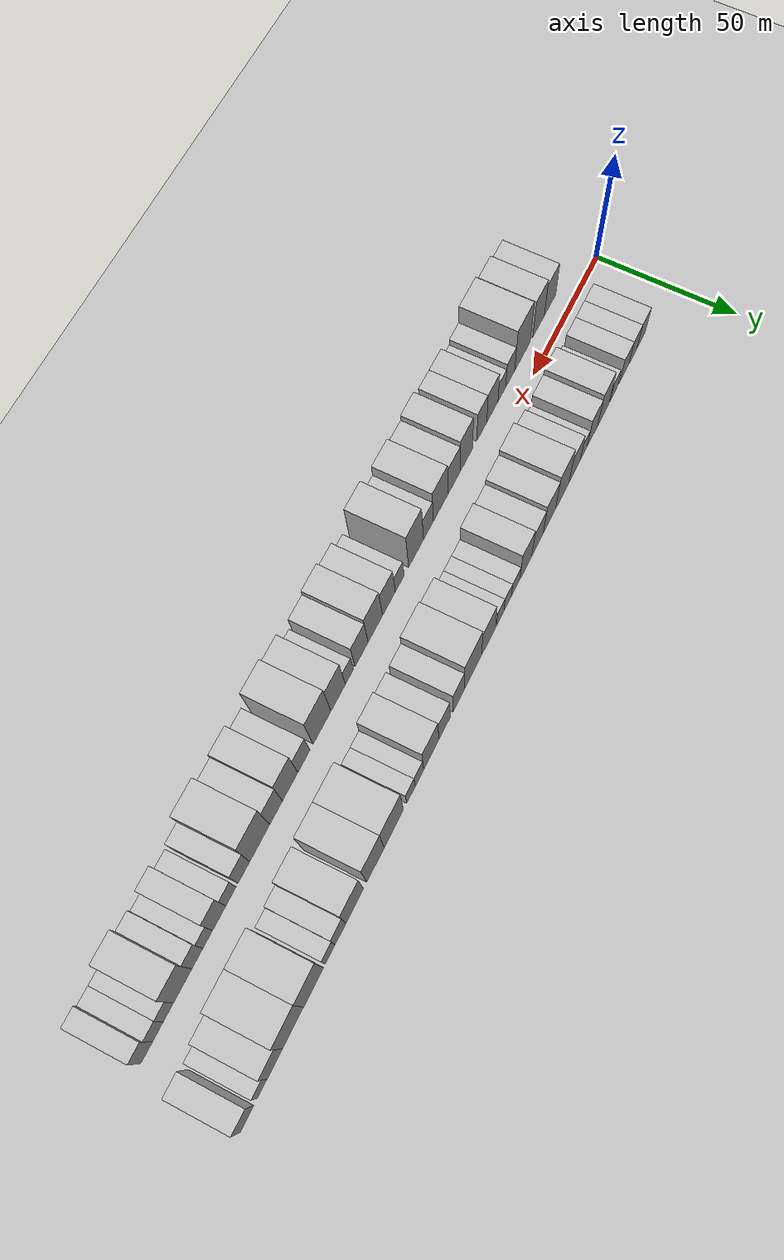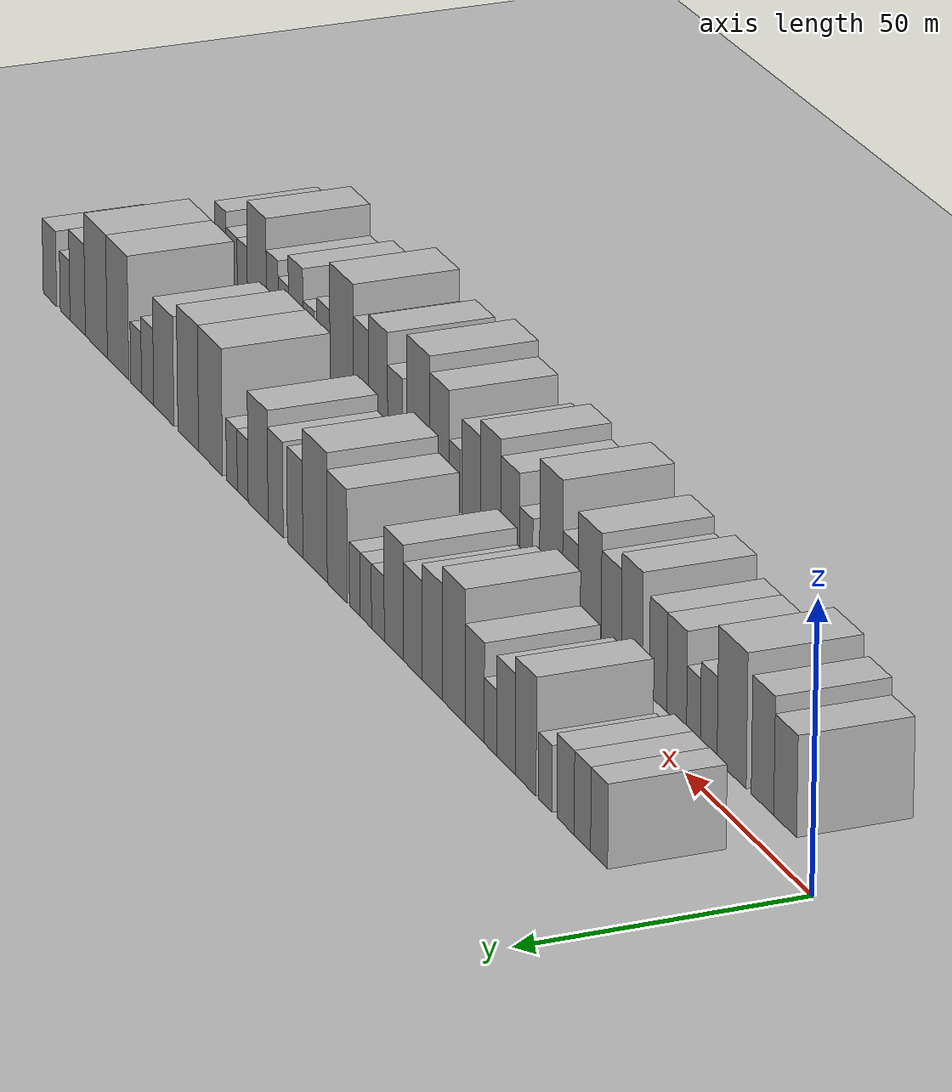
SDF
<?xml version="1.0" encoding="utf-8"?>

<sdf version="1.6">

   <world name="default">

      <gui fullscreen="0">

         <camera name="user_camera">

            <pose>-15 0 4.57585 0 0 0</pose>

            <view_controller>orbit</view_controller>

         </camera>

      </gui>

      <scene>

         <sky>

           <clouds>

             <speed>12</speed>

           </clouds>

         </sky>

         <ambient>0.4 0.4 0.4 1</ambient>

         <background>0.7 0.7 0.7 1</background>

         <shadows>1</shadows>

      </scene>

      <gravity>0 0 -9.8066</gravity>

      <magnetic_field>6e-06 2.3e-05 -4.2e-05</magnetic_field>

      <physics default="0" name="default_physics" type="ode">

         <ode>

            <solver>

               <type>quick</type>

               <iters>10</iters>

               <sor>1.0</sor>

               <use_dynamic_moi_rescaling>0</use_dynamic_moi_rescaling>

            </solver>

            <constraints>

               <cfm>0</cfm>

               <erp>0.2</erp>

               <contact_max_correcting_vel>100</contact_max_correcting_vel>

               <contact_surface_layer>0.001</contact_surface_layer>

            </constraints>

         </ode>

         <max_step_size>0.004</max_step_size>

         <real_time_factor>1</real_time_factor>

         <real_time_update_rate>250</real_time_update_rate>

      </physics>

      <light name="sun" type="directional">

         <cast_shadows>1</cast_shadows>

         <pose>0 0 10 0 0 0</pose>

         <diffuse>0.8 0.8 0.8 1</diffuse>

         <specular>0.2 0.2 0.2 1</specular>

         <attenuation>

            <range>1000</range>

            <constant>0.9</constant>

            <linear>0.01</linear>

            <quadratic>0.001</quadratic>

         </attenuation>

         <direction>-0.5 0.1 -0.9</direction>

      </light>

      <include>

         <name>ground_plane_1</name>

         <uri>model://HANNAS_ground_plane</uri>

         <pose>0 0 0  0 0 0</pose>

      </include>

      <include>

         <name>ground_plane_2</name>

         <uri>model://HANNAS_ground_plane</uri>

         <pose>100 0 0  0 0 0</pose>

      </include>

      <model name="building_1">

         <static>1</static>

         <pose frame="">23.4662 16.0000 0 0.000000 0.000000 1.570796</pose>

         <link name="link">

            <pose frame="">0 0 7.50 0 0 0</pose>

            <collision name="collision">

               <geometry>

                  <box>

                     <size>20.0000 6.9323 15.0000</size>

                  </box>

               </geometry>

               <max_contacts>10</max_contacts>

               <surface>

                  <contact>

                     <ode/>

                  </contact>

                  <bounce/>

                  <friction>

                     <torsional>

                        <ode/>

                     </torsional>

                     <ode/>

                  </friction>

               </surface>

            </collision>

            <visual name="visual">

               <cast_shadows>0</cast_shadows>

               <geometry>

                  <box>

                     <size>20.0000 6.9323 15.0000</size>

                  </box>

               </geometry>

               <material>

                  <script>

                     <uri>model://HANNAS_wall/materials/scripts</uri>

                     <uri>model://HANNAS_wall/materials/textures</uri>

                     <name>vrc/HANNAS_wall</name>

                  </script>

               </material>

            </visual>

            <self_collide>0</self_collide>

            <enable_wind>0</enable_wind>

            <kinematic>0</kinematic>

         </link>

      </model>

      <model name="building_2">

         <static>1</static>

         <pose frame="">30.3055 16.0000 0 0.000000 0.000000 1.570796</pose>

         <link name="link">

            <pose frame="">0 0 7.50 0 0 0</pose>

            <collision name="collision">

               <geometry>

                  <box>

                     <size>20.0000 6.7464 15.0000</size>

                  </box>

               </geometry>

               <max_contacts>10</max_contacts>

               <surface>

                  <contact>

                     <ode/>

                  </contact>

                  <bounce/>

                  <friction>

                     <torsional>

                        <ode/>

                     </torsional>

                     <ode/>

                  </friction>

               </surface>

            </collision>

            <visual name="visual">

               <cast_shadows>0</cast_shadows>

               <geometry>

                  <box>

                     <size>20.0000 6.7464 15.0000</size>

                  </box>

               </geometry>

               <material>

                  <script>

                     <uri>model://HANNAS_wall/materials/scripts</uri>

                     <uri>model://HANNAS_wall/materials/textures</uri>

                     <name>vrc/HANNAS_wall</name>

                  </script>

               </material>

            </visual>

            <self_collide>0</self_collide>

            <enable_wind>0</enable_wind>

            <kinematic>0</kinematic>

         </link>

      </model>

      <model name="building_3">

         <static>1</static>

         <pose frame="">37.2705 16.0000 0 0.000000 0.000000 1.570796</pose>

         <link name="link">

            <pose frame="">0 0 7.50 0 0 0</pose>

            <collision name="collision">

               <geometry>

                  <box>

                     <size>20.0000 7.1836 15.0000</size>

                  </box>

               </geometry>

               <max_contacts>10</max_contacts>

               <surface>

                  <contact>

                     <ode/>

                  </contact>

                  <bounce/>

                  <friction>

                     <torsional>

                        <ode/>

                     </torsional>

                     <ode/>

                  </friction>

               </surface>

            </collision>

            <visual name="visual">

               <cast_shadows>0</cast_shadows>

               <geometry>

                  <box>

                     <size>20.0000 7.1836 15.0000</size>

                  </box>

               </geometry>

               <material>

                  <script>

                     <uri>model://HANNAS_wall/materials/scripts</uri>

                     <uri>model://HANNAS_wall/materials/textures</uri>

                     <name>vrc/HANNAS_wall</name>

                  </script>

               </material>

            </visual>

            <self_collide>0</self_collide>

            <enable_wind>0</enable_wind>

            <kinematic>0</kinematic>

         </link>

      </model>

      <model name="building_4">

         <static>1</static>

         <pose frame="">45.6814 16.0000 0 0.000000 0.000000 1.570796</pose>

         <link name="link">

            <pose frame="">0 0 6.00 0 0 0</pose>

            <collision name="collision">

               <geometry>

                  <box>

                     <size>20.0000 5.6382 12.0000</size>

                  </box>

               </geometry>

               <max_contacts>10</max_contacts>

               <surface>

                  <contact>

                     <ode/>

                  </contact>

                  <bounce/>

                  <friction>

                     <torsional>

                        <ode/>

                     </torsional>

                     <ode/>

                  </friction>

               </surface>

            </collision>

            <visual name="visual">

               <cast_shadows>0</cast_shadows>

               <geometry>

                  <box>

                     <size>20.0000 5.6382 12.0000</size>

                  </box>

               </geometry>

               <material>

                  <script>

                     <uri>model://HANNAS_wall/materials/scripts</uri>

                     <uri>model://HANNAS_wall/materials/textures</uri>

                     <name>vrc/HANNAS_wall</name>

                  </script>

               </material>

            </visual>

            <self_collide>0</self_collide>

            <enable_wind>0</enable_wind>

            <kinematic>0</kinematic>

         </link>

      </model>

      <model name="building_5">

         <static>1</static>

         <pose frame="">53.8715 16.0000 0 0.000000 0.000000 1.570796</pose>

         <link name="link">

            <pose frame="">0 0 10.50 0 0 0</pose>

            <collision name="collision">

               <geometry>

                  <box>

                     <size>20.0000 8.7419 21.0000</size>

                  </box>

               </geometry>

               <max_contacts>10</max_contacts>

               <surface>

                  <contact>

                     <ode/>

                  </contact>

                  <bounce/>

                  <friction>

                     <torsional>

                        <ode/>

                     </torsional>

                     <ode/>

                  </friction>

               </surface>

            </collision>

            <visual name="visual">

               <cast_shadows>0</cast_shadows>

               <geometry>

                  <box>

                     <size>20.0000 8.7419 21.0000</size>

                  </box>

               </geometry>

               <material>

                  <script>

                     <uri>model://HANNAS_wall/materials/scripts</uri>

                     <uri>model://HANNAS_wall/materials/textures</uri>

                     <name>vrc/HANNAS_wall</name>

                  </script>

               </material>

            </visual>

            <self_collide>0</self_collide>

            <enable_wind>0</enable_wind>

            <kinematic>0</kinematic>

         </link>

      </model>

      <model name="building_6">

         <static>1</static>

         <pose frame="">62.2580 16.0000 0 0.000000 0.000000 1.570796</pose>

         <link name="link">

            <pose frame="">0 0 9.00 0 0 0</pose>

            <collision name="collision">

               <geometry>

                  <box>

                     <size>20.0000 8.0312 18.0000</size>

                  </box>

               </geometry>

               <max_contacts>10</max_contacts>

               <surface>

                  <contact>

                     <ode/>

                  </contact>

                  <bounce/>

                  <friction>

                     <torsional>

                        <ode/>

                     </torsional>

                     <ode/>

                  </friction>

               </surface>

            </collision>

            <visual name="visual">

               <cast_shadows>0</cast_shadows>

               <geometry>

                  <box>

                     <size>20.0000 8.0312 18.0000</size>

                  </box>

               </geometry>

               <material>

                  <script>

                     <uri>model://HANNAS_wall/materials/scripts</uri>

                     <uri>model://HANNAS_wall/materials/textures</uri>

                     <name>vrc/HANNAS_wall</name>

                  </script>

               </material>

            </visual>

            <self_collide>0</self_collide>

            <enable_wind>0</enable_wind>

            <kinematic>0</kinematic>

         </link>

      </model>

      <model name="building_7">

         <static>1</static>

         <pose frame="">68.9235 16.0000 0 0.000000 0.000000 1.570796</pose>

         <link name="link">

            <pose frame="">0 0 6.00 0 0 0</pose>

            <collision name="collision">

               <geometry>

                  <box>

                     <size>20.0000 5.2998 12.0000</size>

                  </box>

               </geometry>

               <max_contacts>10</max_contacts>

               <surface>

                  <contact>

                     <ode/>

                  </contact>

                  <bounce/>

                  <friction>

                     <torsional>

                        <ode/>

                     </torsional>

                     <ode/>

                  </friction>

               </surface>

            </collision>

            <visual name="visual">

               <cast_shadows>0</cast_shadows>

               <geometry>

                  <box>

                     <size>20.0000 5.2998 12.0000</size>

                  </box>

               </geometry>

               <material>

                  <script>

                     <uri>model://HANNAS_wall/materials/scripts</uri>

                     <uri>model://HANNAS_wall/materials/textures</uri>

                     <name>vrc/HANNAS_wall</name>

                  </script>

               </material>

            </visual>

            <self_collide>0</self_collide>

            <enable_wind>0</enable_wind>

            <kinematic>0</kinematic>

         </link>

      </model>

      <model name="building_8">

         <static>1</static>

         <pose frame="">75.7848 16.0000 0 0.000000 0.000000 1.570796</pose>

         <link name="link">

            <pose frame="">0 0 9.00 0 0 0</pose>

            <collision name="collision">

               <geometry>

                  <box>

                     <size>20.0000 8.4229 18.0000</size>

                  </box>

               </geometry>

               <max_contacts>10</max_contacts>

               <surface>

                  <contact>

                     <ode/>

                  </contact>

                  <bounce/>

                  <friction>

                     <torsional>

                        <ode/>

                     </torsional>

                     <ode/>

                  </friction>

               </surface>

            </collision>

            <visual name="visual">

               <cast_shadows>0</cast_shadows>

               <geometry>

                  <box>

                     <size>20.0000 8.4229 18.0000</size>

                  </box>

               </geometry>

               <material>

                  <script>

                     <uri>model://HANNAS_wall/materials/scripts</uri>

                     <uri>model://HANNAS_wall/materials/textures</uri>

                     <name>vrc/HANNAS_wall</name>

                  </script>

               </material>

            </visual>

            <self_collide>0</self_collide>

            <enable_wind>0</enable_wind>

            <kinematic>0</kinematic>

         </link>

      </model>

      <model name="building_9">

         <static>1</static>

         <pose frame="">85.0239 16.0000 0 0.000000 0.000000 1.570796</pose>

         <link name="link">

            <pose frame="">0 0 12.00 0 0 0</pose>

            <collision name="collision">

               <geometry>

                  <box>

                     <size>20.0000 10.0552 24.0000</size>

                  </box>

               </geometry>

               <max_contacts>10</max_contacts>

               <surface>

                  <contact>

                     <ode/>

                  </contact>

                  <bounce/>

                  <friction>

                     <torsional>

                        <ode/>

                     </torsional>

                     <ode/>

                  </friction>

               </surface>

            </collision>

            <visual name="visual">

               <cast_shadows>0</cast_shadows>

               <geometry>

                  <box>

                     <size>20.0000 10.0552 24.0000</size>

                  </box>

               </geometry>

               <material>

                  <script>

                     <uri>model://HANNAS_wall/materials/scripts</uri>

                     <uri>model://HANNAS_wall/materials/textures</uri>

                     <name>vrc/HANNAS_wall</name>

                  </script>

               </material>

            </visual>

            <self_collide>0</self_collide>

            <enable_wind>0</enable_wind>

            <kinematic>0</kinematic>

         </link>

      </model>

      <model name="building_10">

         <static>1</static>

         <pose frame="">94.5617 16.0000 0 0.000000 0.000000 1.570796</pose>

         <link name="link">

            <pose frame="">0 0 10.50 0 0 0</pose>

            <collision name="collision">

               <geometry>

                  <box>

                     <size>20.0000 9.0204 21.0000</size>

                  </box>

               </geometry>

               <max_contacts>10</max_contacts>

               <surface>

                  <contact>

                     <ode/>

                  </contact>

                  <bounce/>

                  <friction>

                     <torsional>

                        <ode/>

                     </torsional>

                     <ode/>

                  </friction>

               </surface>

            </collision>

            <visual name="visual">

               <cast_shadows>0</cast_shadows>

               <geometry>

                  <box>

                     <size>20.0000 9.0204 21.0000</size>

                  </box>

               </geometry>

               <material>

                  <script>

                     <uri>model://HANNAS_wall/materials/scripts</uri>

                     <uri>model://HANNAS_wall/materials/textures</uri>

                     <name>vrc/HANNAS_wall</name>

                  </script>

               </material>

            </visual>

            <self_collide>0</self_collide>

            <enable_wind>0</enable_wind>

            <kinematic>0</kinematic>

         </link>

      </model>

      <model name="building_11">

         <static>1</static>

         <pose frame="">103.1988 16.0000 0 0.000000 0.000000 1.570796</pose>

         <link name="link">

            <pose frame="">0 0 9.00 0 0 0</pose>

            <collision name="collision">

               <geometry>

                  <box>

                     <size>20.0000 8.2538 18.0000</size>

                  </box>

               </geometry>

               <max_contacts>10</max_contacts>

               <surface>

                  <contact>

                     <ode/>

                  </contact>

                  <bounce/>

                  <friction>

                     <torsional>

                        <ode/>

                     </torsional>

                     <ode/>

                  </friction>

               </surface>

            </collision>

            <visual name="visual">

               <cast_shadows>0</cast_shadows>

               <geometry>

                  <box>

                     <size>20.0000 8.2538 18.0000</size>

                  </box>

               </geometry>

               <material>

                  <script>

                     <uri>model://HANNAS_wall/materials/scripts</uri>

                     <uri>model://HANNAS_wall/materials/textures</uri>

                     <name>vrc/HANNAS_wall</name>

                  </script>

               </material>

            </visual>

            <self_collide>0</self_collide>

            <enable_wind>0</enable_wind>

            <kinematic>0</kinematic>

         </link>

      </model>

      <model name="building_12">

         <static>1</static>

         <pose frame="">111.6515 16.0000 0 0.000000 0.000000 1.570796</pose>

         <link name="link">

            <pose frame="">0 0 10.50 0 0 0</pose>

            <collision name="collision">

               <geometry>

                  <box>

                     <size>20.0000 8.6517 21.0000</size>

                  </box>

               </geometry>

               <max_contacts>10</max_contacts>

               <surface>

                  <contact>

                     <ode/>

                  </contact>

                  <bounce/>

                  <friction>

                     <torsional>

                        <ode/>

                     </torsional>

                     <ode/>

                  </friction>

               </surface>

            </collision>

            <visual name="visual">

               <cast_shadows>0</cast_shadows>

               <geometry>

                  <box>

                     <size>20.0000 8.6517 21.0000</size>

                  </box>

               </geometry>

               <material>

                  <script>

                     <uri>model://HANNAS_wall/materials/scripts</uri>

                     <uri>model://HANNAS_wall/materials/textures</uri>

                     <name>vrc/HANNAS_wall</name>

                  </script>

               </material>

            </visual>

            <self_collide>0</self_collide>

            <enable_wind>0</enable_wind>

            <kinematic>0</kinematic>

         </link>

      </model>

      <model name="building_13">

         <static>1</static>

         <pose frame="">118.8932 16.0000 0 0.000000 0.000000 1.570796</pose>

         <link name="link">

            <pose frame="">0 0 6.00 0 0 0</pose>

            <collision name="collision">

               <geometry>

                  <box>

                     <size>20.0000 5.8317 12.0000</size>

                  </box>

               </geometry>

               <max_contacts>10</max_contacts>

               <surface>

                  <contact>

                     <ode/>

                  </contact>

                  <bounce/>

                  <friction>

                     <torsional>

                        <ode/>

                     </torsional>

                     <ode/>

                  </friction>

               </surface>

            </collision>

            <visual name="visual">

               <cast_shadows>0</cast_shadows>

               <geometry>

                  <box>

                     <size>20.0000 5.8317 12.0000</size>

                  </box>

               </geometry>

               <material>

                  <script>

                     <uri>model://HANNAS_wall/materials/scripts</uri>

                     <uri>model://HANNAS_wall/materials/textures</uri>

                     <name>vrc/HANNAS_wall</name>

                  </script>

               </material>

            </visual>

            <self_collide>0</self_collide>

            <enable_wind>0</enable_wind>

            <kinematic>0</kinematic>

         </link>

      </model>

      <model name="building_14">

         <static>1</static>

         <pose frame="">124.3802 16.0000 0 0.000000 0.000000 1.570796</pose>

         <link name="link">

            <pose frame="">0 0 6.00 0 0 0</pose>

            <collision name="collision">

               <geometry>

                  <box>

                     <size>20.0000 5.1422 12.0000</size>

                  </box>

               </geometry>

               <max_contacts>10</max_contacts>

               <surface>

                  <contact>

                     <ode/>

                  </contact>

                  <bounce/>

                  <friction>

                     <torsional>

                        <ode/>

                     </torsional>

                     <ode/>

                  </friction>

               </surface>

            </collision>

            <visual name="visual">

               <cast_shadows>0</cast_shadows>

               <geometry>

                  <box>

                     <size>20.0000 5.1422 12.0000</size>

                  </box>

               </geometry>

               <material>

                  <script>

                     <uri>model://HANNAS_wall/materials/scripts</uri>

                     <uri>model://HANNAS_wall/materials/textures</uri>

                     <name>vrc/HANNAS_wall</name>

                  </script>

               </material>

            </visual>

            <self_collide>0</self_collide>

            <enable_wind>0</enable_wind>

            <kinematic>0</kinematic>

         </link>

      </model>

      <model name="building_15">

         <static>1</static>

         <pose frame="">129.4911 16.0000 0 0.000000 0.000000 1.570796</pose>

         <link name="link">

            <pose frame="">0 0 6.00 0 0 0</pose>

            <collision name="collision">

               <geometry>

                  <box>

                     <size>20.0000 5.0797 12.0000</size>

                  </box>

               </geometry>

               <max_contacts>10</max_contacts>

               <surface>

                  <contact>

                     <ode/>

                  </contact>

                  <bounce/>

                  <friction>

                     <torsional>

                        <ode/>

                     </torsional>

                     <ode/>

                  </friction>

               </surface>

            </collision>

            <visual name="visual">

               <cast_shadows>0</cast_shadows>

               <geometry>

                  <box>

                     <size>20.0000 5.0797 12.0000</size>

                  </box>

               </geometry>

               <material>

                  <script>

                     <uri>model://HANNAS_wall/materials/scripts</uri>

                     <uri>model://HANNAS_wall/materials/textures</uri>

                     <name>vrc/HANNAS_wall</name>

                  </script>

               </material>

            </visual>

            <self_collide>0</self_collide>

            <enable_wind>0</enable_wind>

            <kinematic>0</kinematic>

         </link>

      </model>

      <model name="building_16">

         <static>1</static>

         <pose frame="">137.6855 16.0000 0 0.000000 0.000000 1.570796</pose>

         <link name="link">

            <pose frame="">0 0 10.50 0 0 0</pose>

            <collision name="collision">

               <geometry>

                  <box>

                     <size>20.0000 9.3090 21.0000</size>

                  </box>

               </geometry>

               <max_contacts>10</max_contacts>

               <surface>

                  <contact>

                     <ode/>

                  </contact>

                  <bounce/>

                  <friction>

                     <torsional>

                        <ode/>

                     </torsional>

                     <ode/>

                  </friction>

               </surface>

            </collision>

            <visual name="visual">

               <cast_shadows>0</cast_shadows>

               <geometry>

                  <box>

                     <size>20.0000 9.3090 21.0000</size>

                  </box>

               </geometry>

               <material>

                  <script>

                     <uri>model://HANNAS_wall/materials/scripts</uri>

                     <uri>model://HANNAS_wall/materials/textures</uri>

                     <name>vrc/HANNAS_wall</name>

                  </script>

               </material>

            </visual>

            <self_collide>0</self_collide>

            <enable_wind>0</enable_wind>

            <kinematic>0</kinematic>

         </link>

      </model>

      <model name="building_17">

         <static>1</static>

         <pose frame="">148.1238 16.0000 0 0.000000 0.000000 1.570796</pose>

         <link name="link">

            <pose frame="">0 0 12.00 0 0 0</pose>

            <collision name="collision">

               <geometry>

                  <box>

                     <size>20.0000 11.5676 24.0000</size>

                  </box>

               </geometry>

               <max_contacts>10</max_contacts>

               <surface>

                  <contact>

                     <ode/>

                  </contact>

                  <bounce/>

                  <friction>

                     <torsional>

                        <ode/>

                     </torsional>

                     <ode/>

                  </friction>

               </surface>

            </collision>

            <visual name="visual">

               <cast_shadows>0</cast_shadows>

               <geometry>

                  <box>

                     <size>20.0000 11.5676 24.0000</size>

                  </box>

               </geometry>

               <material>

                  <script>

                     <uri>model://HANNAS_wall/materials/scripts</uri>

                     <uri>model://HANNAS_wall/materials/textures</uri>

                     <name>vrc/HANNAS_wall</name>

                  </script>

               </material>

            </visual>

            <self_collide>0</self_collide>

            <enable_wind>0</enable_wind>

            <kinematic>0</kinematic>

         </link>

      </model>

      <model name="building_18">

         <static>1</static>

         <pose frame="">157.6105 16.0000 0 0.000000 0.000000 1.570796</pose>

         <link name="link">

            <pose frame="">0 0 9.00 0 0 0</pose>

            <collision name="collision">

               <geometry>

                  <box>

                     <size>20.0000 7.4056 18.0000</size>

                  </box>

               </geometry>

               <max_contacts>10</max_contacts>

               <surface>

                  <contact>

                     <ode/>

                  </contact>

                  <bounce/>

                  <friction>

                     <torsional>

                        <ode/>

                     </torsional>

                     <ode/>

                  </friction>

               </surface>

            </collision>

            <visual name="visual">

               <cast_shadows>0</cast_shadows>

               <geometry>

                  <box>

                     <size>20.0000 7.4056 18.0000</size>

                  </box>

               </geometry>

               <material>

                  <script>

                     <uri>model://HANNAS_wall/materials/scripts</uri>

                     <uri>model://HANNAS_wall/materials/textures</uri>

                     <name>vrc/HANNAS_wall</name>

                  </script>

               </material>

            </visual>

            <self_collide>0</self_collide>

            <enable_wind>0</enable_wind>

            <kinematic>0</kinematic>

         </link>

      </model>

      <model name="building_19">

         <static>1</static>

         <pose frame="">166.9849 16.0000 0 0.000000 0.000000 1.570796</pose>

         <link name="link">

            <pose frame="">0 0 9.00 0 0 0</pose>

            <collision name="collision">

               <geometry>

                  <box>

                     <size>20.0000 7.3432 18.0000</size>

                  </box>

               </geometry>

               <max_contacts>10</max_contacts>

               <surface>

                  <contact>

                     <ode/>

                  </contact>

                  <bounce/>

                  <friction>

                     <torsional>

                        <ode/>

                     </torsional>

                     <ode/>

                  </friction>

               </surface>

            </collision>

            <visual name="visual">

               <cast_shadows>0</cast_shadows>

               <geometry>

                  <box>

                     <size>20.0000 7.3432 18.0000</size>

                  </box>

               </geometry>

               <material>

                  <script>

                     <uri>model://HANNAS_wall/materials/scripts</uri>

                     <uri>model://HANNAS_wall/materials/textures</uri>

                     <name>vrc/HANNAS_wall</name>

                  </script>

               </material>

            </visual>

            <self_collide>0</self_collide>

            <enable_wind>0</enable_wind>

            <kinematic>0</kinematic>

         </link>

      </model>

      <model name="building_20">

         <static>1</static>

         <pose frame="">175.5093 16.0000 0 0.000000 0.000000 1.570796</pose>

         <link name="link">

            <pose frame="">0 0 10.50 0 0 0</pose>

            <collision name="collision">

               <geometry>

                  <box>

                     <size>20.0000 9.7057 21.0000</size>

                  </box>

               </geometry>

               <max_contacts>10</max_contacts>

               <surface>

                  <contact>

                     <ode/>

                  </contact>

                  <bounce/>

                  <friction>

                     <torsional>

                        <ode/>

                     </torsional>

                     <ode/>

                  </friction>

               </surface>

            </collision>

            <visual name="visual">

               <cast_shadows>0</cast_shadows>

               <geometry>

                  <box>

                     <size>20.0000 9.7057 21.0000</size>

                  </box>

               </geometry>

               <material>

                  <script>

                     <uri>model://HANNAS_wall/materials/scripts</uri>

                     <uri>model://HANNAS_wall/materials/textures</uri>

                     <name>vrc/HANNAS_wall</name>

                  </script>

               </material>

            </visual>

            <self_collide>0</self_collide>

            <enable_wind>0</enable_wind>

            <kinematic>0</kinematic>

         </link>

      </model>

      <model name="building_21">

         <static>1</static>

         <pose frame="">183.0260 16.0000 0 0.000000 0.000000 1.570796</pose>

         <link name="link">

            <pose frame="">0 0 6.00 0 0 0</pose>

            <collision name="collision">

               <geometry>

                  <box>

                     <size>20.0000 5.3277 12.0000</size>

                  </box>

               </geometry>

               <max_contacts>10</max_contacts>

               <surface>

                  <contact>

                     <ode/>

                  </contact>

                  <bounce/>

                  <friction>

                     <torsional>

                        <ode/>

                     </torsional>

                     <ode/>

                  </friction>

               </surface>

            </collision>

            <visual name="visual">

               <cast_shadows>0</cast_shadows>

               <geometry>

                  <box>

                     <size>20.0000 5.3277 12.0000</size>

                  </box>

               </geometry>

               <material>

                  <script>

                     <uri>model://HANNAS_wall/materials/scripts</uri>

                     <uri>model://HANNAS_wall/materials/textures</uri>

                     <name>vrc/HANNAS_wall</name>

                  </script>

               </material>

            </visual>

            <self_collide>0</self_collide>

            <enable_wind>0</enable_wind>

            <kinematic>0</kinematic>

         </link>

      </model>

      <model name="building_22">

         <static>1</static>

         <pose frame="">188.3907 16.0000 0 0.000000 0.000000 1.570796</pose>

         <link name="link">

            <pose frame="">0 0 6.00 0 0 0</pose>

            <collision name="collision">

               <geometry>

                  <box>

                     <size>20.0000 5.4015 12.0000</size>

                  </box>

               </geometry>

               <max_contacts>10</max_contacts>

               <surface>

                  <contact>

                     <ode/>

                  </contact>

                  <bounce/>

                  <friction>

                     <torsional>

                        <ode/>

                     </torsional>

                     <ode/>

                  </friction>

               </surface>

            </collision>

            <visual name="visual">

               <cast_shadows>0</cast_shadows>

               <geometry>

                  <box>

                     <size>20.0000 5.4015 12.0000</size>

                  </box>

               </geometry>

               <material>

                  <script>

                     <uri>model://HANNAS_wall/materials/scripts</uri>

                     <uri>model://HANNAS_wall/materials/textures</uri>

                     <name>vrc/HANNAS_wall</name>

                  </script>

               </material>

            </visual>

            <self_collide>0</self_collide>

            <enable_wind>0</enable_wind>

            <kinematic>0</kinematic>

         </link>

      </model>

      <model name="building_23">

         <static>1</static>

         <pose frame="">199.0637 16.0000 0 0.000000 0.000000 1.570796</pose>

         <link name="link">

            <pose frame="">0 0 12.00 0 0 0</pose>

            <collision name="collision">

               <geometry>

                  <box>

                     <size>20.0000 11.9444 24.0000</size>

                  </box>

               </geometry>

               <max_contacts>10</max_contacts>

               <surface>

                  <contact>

                     <ode/>

                  </contact>

                  <bounce/>

                  <friction>

                     <torsional>

                        <ode/>

                     </torsional>

                     <ode/>

                  </friction>

               </surface>

            </collision>

            <visual name="visual">

               <cast_shadows>0</cast_shadows>

               <geometry>

                  <box>

                     <size>20.0000 11.9444 24.0000</size>

                  </box>

               </geometry>

               <material>

                  <script>

                     <uri>model://HANNAS_wall/materials/scripts</uri>

                     <uri>model://HANNAS_wall/materials/textures</uri>

                     <name>vrc/HANNAS_wall</name>

                  </script>

               </material>

            </visual>

            <self_collide>0</self_collide>

            <enable_wind>0</enable_wind>

            <kinematic>0</kinematic>

         </link>

      </model>

      <model name="building_24">

         <static>1</static>

         <pose frame="">210.3051 16.0000 0 0.000000 0.000000 1.570796</pose>

         <link name="link">

            <pose frame="">0 0 12.00 0 0 0</pose>

            <collision name="collision">

               <geometry>

                  <box>

                     <size>20.0000 10.5384 24.0000</size>

                  </box>

               </geometry>

               <max_contacts>10</max_contacts>

               <surface>

                  <contact>

                     <ode/>

                  </contact>

                  <bounce/>

                  <friction>

                     <torsional>

                        <ode/>

                     </torsional>

                     <ode/>

                  </friction>

               </surface>

            </collision>

            <visual name="visual">

               <cast_shadows>0</cast_shadows>

               <geometry>

                  <box>

                     <size>20.0000 10.5384 24.0000</size>

                  </box>

               </geometry>

               <material>

                  <script>

                     <uri>model://HANNAS_wall/materials/scripts</uri>

                     <uri>model://HANNAS_wall/materials/textures</uri>

                     <name>vrc/HANNAS_wall</name>

                  </script>

               </material>

            </visual>

            <self_collide>0</self_collide>

            <enable_wind>0</enable_wind>

            <kinematic>0</kinematic>

         </link>

      </model>

      <model name="building_25">

         <static>1</static>

         <pose frame="">222.7786 16.0000 0 0.000000 0.000000 1.570796</pose>

         <link name="link">

            <pose frame="">0 0 10.50 0 0 0</pose>

            <collision name="collision">

               <geometry>

                  <box>

                     <size>20.0000 10.4088 21.0000</size>

                  </box>

               </geometry>

               <max_contacts>10</max_contacts>

               <surface>

                  <contact>

                     <ode/>

                  </contact>

                  <bounce/>

                  <friction>

                     <torsional>

                        <ode/>

                     </torsional>

                     <ode/>

                  </friction>

               </surface>

            </collision>

            <visual name="visual">

               <cast_shadows>0</cast_shadows>

               <geometry>

                  <box>

                     <size>20.0000 10.4088 21.0000</size>

                  </box>

               </geometry>

               <material>

                  <script>

                     <uri>model://HANNAS_wall/materials/scripts</uri>

                     <uri>model://HANNAS_wall/materials/textures</uri>

                     <name>vrc/HANNAS_wall</name>

                  </script>

               </material>

            </visual>

            <self_collide>0</self_collide>

            <enable_wind>0</enable_wind>

            <kinematic>0</kinematic>

         </link>

      </model>

      <model name="building_26">

         <static>1</static>

         <pose frame="">231.1399 16.0000 0 0.000000 0.000000 1.570796</pose>

         <link name="link">

            <pose frame="">0 0 7.50 0 0 0</pose>

            <collision name="collision">

               <geometry>

                  <box>

                     <size>20.0000 6.3137 15.0000</size>

                  </box>

               </geometry>

               <max_contacts>10</max_contacts>

               <surface>

                  <contact>

                     <ode/>

                  </contact>

                  <bounce/>

                  <friction>

                     <torsional>

                        <ode/>

                     </torsional>

                     <ode/>

                  </friction>

               </surface>

            </collision>

            <visual name="visual">

               <cast_shadows>0</cast_shadows>

               <geometry>

                  <box>

                     <size>20.0000 6.3137 15.0000</size>

                  </box>

               </geometry>

               <material>

                  <script>

                     <uri>model://HANNAS_wall/materials/scripts</uri>

                     <uri>model://HANNAS_wall/materials/textures</uri>

                     <name>vrc/HANNAS_wall</name>

                  </script>

               </material>

            </visual>

            <self_collide>0</self_collide>

            <enable_wind>0</enable_wind>

            <kinematic>0</kinematic>

         </link>

      </model>

      <model name="building_27">

         <static>1</static>

         <pose frame="">237.1442 16.0000 0 0.000000 0.000000 1.570796</pose>

         <link name="link">

            <pose frame="">0 0 6.00 0 0 0</pose>

            <collision name="collision">

               <geometry>

                  <box>

                     <size>20.0000 5.6949 12.0000</size>

                  </box>

               </geometry>

               <max_contacts>10</max_contacts>

               <surface>

                  <contact>

                     <ode/>

                  </contact>

                  <bounce/>

                  <friction>

                     <torsional>

                        <ode/>

                     </torsional>

                     <ode/>

                  </friction>

               </surface>

            </collision>

            <visual name="visual">

               <cast_shadows>0</cast_shadows>

               <geometry>

                  <box>

                     <size>20.0000 5.6949 12.0000</size>

                  </box>

               </geometry>

               <material>

                  <script>

                     <uri>model://HANNAS_wall/materials/scripts</uri>

                     <uri>model://HANNAS_wall/materials/textures</uri>

                     <name>vrc/HANNAS_wall</name>

                  </script>

               </material>

            </visual>

            <self_collide>0</self_collide>

            <enable_wind>0</enable_wind>

            <kinematic>0</kinematic>

         </link>

      </model>

      <model name="building_28">

         <static>1</static>

         <pose frame="">246.6571 16.0000 0 0.000000 0.000000 1.570796</pose>

         <link name="link">

            <pose frame="">0 0 12.00 0 0 0</pose>

            <collision name="collision">

               <geometry>

                  <box>

                     <size>20.0000 11.3309 24.0000</size>

                  </box>

               </geometry>

               <max_contacts>10</max_contacts>

               <surface>

                  <contact>

                     <ode/>

                  </contact>

                  <bounce/>

                  <friction>

                     <torsional>

                        <ode/>

                     </torsional>

                     <ode/>

                  </friction>

               </surface>

            </collision>

            <visual name="visual">

               <cast_shadows>0</cast_shadows>

               <geometry>

                  <box>

                     <size>20.0000 11.3309 24.0000</size>

                  </box>

               </geometry>

               <material>

                  <script>

                     <uri>model://HANNAS_wall/materials/scripts</uri>

                     <uri>model://HANNAS_wall/materials/textures</uri>

                     <name>vrc/HANNAS_wall</name>

                  </script>

               </material>

            </visual>

            <self_collide>0</self_collide>

            <enable_wind>0</enable_wind>

            <kinematic>0</kinematic>

         </link>

      </model>

      <model name="building_29">

         <static>1</static>

         <pose frame="">258.2216 16.0000 0 0.000000 0.000000 1.570796</pose>

         <link name="link">

            <pose frame="">0 0 12.00 0 0 0</pose>

            <collision name="collision">

               <geometry>

                  <box>

                     <size>20.0000 11.7980 24.0000</size>

                  </box>

               </geometry>

               <max_contacts>10</max_contacts>

               <surface>

                  <contact>

                     <ode/>

                  </contact>

                  <bounce/>

                  <friction>

                     <torsional>

                        <ode/>

                     </torsional>

                     <ode/>

                  </friction>

               </surface>

            </collision>

            <visual name="visual">

               <cast_shadows>0</cast_shadows>

               <geometry>

                  <box>

                     <size>20.0000 11.7980 24.0000</size>

                  </box>

               </geometry>

               <material>

                  <script>

                     <uri>model://HANNAS_wall/materials/scripts</uri>

                     <uri>model://HANNAS_wall/materials/textures</uri>

                     <name>vrc/HANNAS_wall</name>

                  </script>

               </material>

            </visual>

            <self_collide>0</self_collide>

            <enable_wind>0</enable_wind>

            <kinematic>0</kinematic>

         </link>

      </model>

      <model name="building_30">

         <static>1</static>

         <pose frame="">268.2903 16.0000 0 0.000000 0.000000 1.570796</pose>

         <link name="link">

            <pose frame="">0 0 9.00 0 0 0</pose>

            <collision name="collision">

               <geometry>

                  <box>

                     <size>20.0000 8.3393 18.0000</size>

                  </box>

               </geometry>

               <max_contacts>10</max_contacts>

               <surface>

                  <contact>

                     <ode/>

                  </contact>

                  <bounce/>

                  <friction>

                     <torsional>

                        <ode/>

                     </torsional>

                     <ode/>

                  </friction>

               </surface>

            </collision>

            <visual name="visual">

               <cast_shadows>0</cast_shadows>

               <geometry>

                  <box>

                     <size>20.0000 8.3393 18.0000</size>

                  </box>

               </geometry>

               <material>

                  <script>

                     <uri>model://HANNAS_wall/materials/scripts</uri>

                     <uri>model://HANNAS_wall/materials/textures</uri>

                     <name>vrc/HANNAS_wall</name>

                  </script>

               </material>

            </visual>

            <self_collide>0</self_collide>

            <enable_wind>0</enable_wind>

            <kinematic>0</kinematic>

         </link>

      </model>

      <model name="building_31">

         <static>1</static>

         <pose frame="">275.1168 16.0000 0 0.000000 0.000000 1.570796</pose>

         <link name="link">

            <pose frame="">0 0 6.00 0 0 0</pose>

            <collision name="collision">

               <geometry>

                  <box>

                     <size>20.0000 5.3137 12.0000</size>

                  </box>

               </geometry>

               <max_contacts>10</max_contacts>

               <surface>

                  <contact>

                     <ode/>

                  </contact>

                  <bounce/>

                  <friction>

                     <torsional>

                        <ode/>

                     </torsional>

                     <ode/>

                  </friction>

               </surface>

            </collision>

            <visual name="visual">

               <cast_shadows>0</cast_shadows>

               <geometry>

                  <box>

                     <size>20.0000 5.3137 12.0000</size>

                  </box>

               </geometry>

               <material>

                  <script>

                     <uri>model://HANNAS_wall/materials/scripts</uri>

                     <uri>model://HANNAS_wall/materials/textures</uri>

                     <name>vrc/HANNAS_wall</name>

                  </script>

               </material>

            </visual>

            <self_collide>0</self_collide>

            <enable_wind>0</enable_wind>

            <kinematic>0</kinematic>

         </link>

      </model>

      <model name="building_32">

         <static>1</static>

         <pose frame="">283.4479 16.0000 0 0.000000 0.000000 1.570796</pose>

         <link name="link">

            <pose frame="">0 0 7.50 0 0 0</pose>

            <collision name="collision">

               <geometry>

                  <box>

                     <size>20.0000 7.3486 15.0000</size>

                  </box>

               </geometry>

               <max_contacts>10</max_contacts>

               <surface>

                  <contact>

                     <ode/>

                  </contact>

                  <bounce/>

                  <friction>

                     <torsional>

                        <ode/>

                     </torsional>

                     <ode/>

                  </friction>

               </surface>

            </collision>

            <visual name="visual">

               <cast_shadows>0</cast_shadows>

               <geometry>

                  <box>

                     <size>20.0000 7.3486 15.0000</size>

                  </box>

               </geometry>

               <material>

                  <script>

                     <uri>model://HANNAS_wall/materials/scripts</uri>

                     <uri>model://HANNAS_wall/materials/textures</uri>

                     <name>vrc/HANNAS_wall</name>

                  </script>

               </material>

            </visual>

            <self_collide>0</self_collide>

            <enable_wind>0</enable_wind>

            <kinematic>0</kinematic>

         </link>

      </model>

      <model name="building_33">

         <static>1</static>

         <pose frame="">24.4826 -16.0000 0 0.000000 0.000000 1.570796</pose>

         <link name="link">

            <pose frame="">0 0 9.00 0 0 0</pose>

            <collision name="collision">

               <geometry>

                  <box>

                     <size>20.0000 8.9652 18.0000</size>

                  </box>

               </geometry>

               <max_contacts>10</max_contacts>

               <surface>

                  <contact>

                     <ode/>

                  </contact>

                  <bounce/>

                  <friction>

                     <torsional>

                        <ode/>

                     </torsional>

                     <ode/>

                  </friction>

               </surface>

            </collision>

            <visual name="visual">

               <cast_shadows>0</cast_shadows>

               <geometry>

                  <box>

                     <size>20.0000 8.9652 18.0000</size>

                  </box>

               </geometry>

               <material>

                  <script>

                     <uri>model://HANNAS_wall/materials/scripts</uri>

                     <uri>model://HANNAS_wall/materials/textures</uri>

                     <name>vrc/HANNAS_wall</name>

                  </script>

               </material>

            </visual>

            <self_collide>0</self_collide>

            <enable_wind>0</enable_wind>

            <kinematic>0</kinematic>

         </link>

      </model>

      <model name="building_34">

         <static>1</static>

         <pose frame="">33.4205 -16.0000 0 0.000000 0.000000 1.570796</pose>

         <link name="link">

            <pose frame="">0 0 10.50 0 0 0</pose>

            <collision name="collision">

               <geometry>

                  <box>

                     <size>20.0000 8.9107 21.0000</size>

                  </box>

               </geometry>

               <max_contacts>10</max_contacts>

               <surface>

                  <contact>

                     <ode/>

                  </contact>

                  <bounce/>

                  <friction>

                     <torsional>

                        <ode/>

                     </torsional>

                     <ode/>

                  </friction>

               </surface>

            </collision>

            <visual name="visual">

               <cast_shadows>0</cast_shadows>

               <geometry>

                  <box>

                     <size>20.0000 8.9107 21.0000</size>

                  </box>

               </geometry>

               <material>

                  <script>

                     <uri>model://HANNAS_wall/materials/scripts</uri>

                     <uri>model://HANNAS_wall/materials/textures</uri>

                     <name>vrc/HANNAS_wall</name>

                  </script>

               </material>

            </visual>

            <self_collide>0</self_collide>

            <enable_wind>0</enable_wind>

            <kinematic>0</kinematic>

         </link>

      </model>

      <model name="building_35">

         <static>1</static>

         <pose frame="">45.7450 -16.0000 0 0.000000 0.000000 1.570796</pose>

         <link name="link">

            <pose frame="">0 0 12.00 0 0 0</pose>

            <collision name="collision">

               <geometry>

                  <box>

                     <size>20.0000 11.7382 24.0000</size>

                  </box>

               </geometry>

               <max_contacts>10</max_contacts>

               <surface>

                  <contact>

                     <ode/>

                  </contact>

                  <bounce/>

                  <friction>

                     <torsional>

                        <ode/>

                     </torsional>

                     <ode/>

                  </friction>

               </surface>

            </collision>

            <visual name="visual">

               <cast_shadows>0</cast_shadows>

               <geometry>

                  <box>

                     <size>20.0000 11.7382 24.0000</size>

                  </box>

               </geometry>

               <material>

                  <script>

                     <uri>model://HANNAS_wall/materials/scripts</uri>

                     <uri>model://HANNAS_wall/materials/textures</uri>

                     <name>vrc/HANNAS_wall</name>

                  </script>

               </material>

            </visual>

            <self_collide>0</self_collide>

            <enable_wind>0</enable_wind>

            <kinematic>0</kinematic>

         </link>

      </model>

      <model name="building_36">

         <static>1</static>

         <pose frame="">55.0073 -16.0000 0 0.000000 0.000000 1.570796</pose>

         <link name="link">

            <pose frame="">0 0 7.50 0 0 0</pose>

            <collision name="collision">

               <geometry>

                  <box>

                     <size>20.0000 6.7863 15.0000</size>

                  </box>

               </geometry>

               <max_contacts>10</max_contacts>

               <surface>

                  <contact>

                     <ode/>

                  </contact>

                  <bounce/>

                  <friction>

                     <torsional>

                        <ode/>

                     </torsional>

                     <ode/>

                  </friction>

               </surface>

            </collision>

            <visual name="visual">

               <cast_shadows>0</cast_shadows>

               <geometry>

                  <box>

                     <size>20.0000 6.7863 15.0000</size>

                  </box>

               </geometry>

               <material>

                  <script>

                     <uri>model://HANNAS_wall/materials/scripts</uri>

                     <uri>model://HANNAS_wall/materials/textures</uri>

                     <name>vrc/HANNAS_wall</name>

                  </script>

               </material>

            </visual>

            <self_collide>0</self_collide>

            <enable_wind>0</enable_wind>

            <kinematic>0</kinematic>

         </link>

      </model>

      <model name="building_37">

         <static>1</static>

         <pose frame="">61.2317 -16.0000 0 0.000000 0.000000 1.570796</pose>

         <link name="link">

            <pose frame="">0 0 6.00 0 0 0</pose>

            <collision name="collision">

               <geometry>

                  <box>

                     <size>20.0000 5.6625 12.0000</size>

                  </box>

               </geometry>

               <max_contacts>10</max_contacts>

               <surface>

                  <contact>

                     <ode/>

                  </contact>

                  <bounce/>

                  <friction>

                     <torsional>

                        <ode/>

                     </torsional>

                     <ode/>

                  </friction>

               </surface>

            </collision>

            <visual name="visual">

               <cast_shadows>0</cast_shadows>

               <geometry>

                  <box>

                     <size>20.0000 5.6625 12.0000</size>

                  </box>

               </geometry>

               <material>

                  <script>

                     <uri>model://HANNAS_wall/materials/scripts</uri>

                     <uri>model://HANNAS_wall/materials/textures</uri>

                     <name>vrc/HANNAS_wall</name>

                  </script>

               </material>

            </visual>

            <self_collide>0</self_collide>

            <enable_wind>0</enable_wind>

            <kinematic>0</kinematic>

         </link>

      </model>

      <model name="building_38">

         <static>1</static>

         <pose frame="">68.1342 -16.0000 0 0.000000 0.000000 1.570796</pose>

         <link name="link">

            <pose frame="">0 0 9.00 0 0 0</pose>

            <collision name="collision">

               <geometry>

                  <box>

                     <size>20.0000 8.1426 18.0000</size>

                  </box>

               </geometry>

               <max_contacts>10</max_contacts>

               <surface>

                  <contact>

                     <ode/>

                  </contact>

                  <bounce/>

                  <friction>

                     <torsional>

                        <ode/>

                     </torsional>

                     <ode/>

                  </friction>

               </surface>

            </collision>

            <visual name="visual">

               <cast_shadows>0</cast_shadows>

               <geometry>

                  <box>

                     <size>20.0000 8.1426 18.0000</size>

                  </box>

               </geometry>

               <material>

                  <script>

                     <uri>model://HANNAS_wall/materials/scripts</uri>

                     <uri>model://HANNAS_wall/materials/textures</uri>

                     <name>vrc/HANNAS_wall</name>

                  </script>

               </material>

            </visual>

            <self_collide>0</self_collide>

            <enable_wind>0</enable_wind>

            <kinematic>0</kinematic>

         </link>

      </model>

      <model name="building_39">

         <static>1</static>

         <pose frame="">75.8522 -16.0000 0 0.000000 0.000000 1.570796</pose>

         <link name="link">

            <pose frame="">0 0 9.00 0 0 0</pose>

            <collision name="collision">

               <geometry>

                  <box>

                     <size>20.0000 7.2933 18.0000</size>

                  </box>

               </geometry>

               <max_contacts>10</max_contacts>

               <surface>

                  <contact>

                     <ode/>

                  </contact>

                  <bounce/>

                  <friction>

                     <torsional>

                        <ode/>

                     </torsional>

                     <ode/>

                  </friction>

               </surface>

            </collision>

            <visual name="visual">

               <cast_shadows>0</cast_shadows>

               <geometry>

                  <box>

                     <size>20.0000 7.2933 18.0000</size>

                  </box>

               </geometry>

               <material>

                  <script>

                     <uri>model://HANNAS_wall/materials/scripts</uri>

                     <uri>model://HANNAS_wall/materials/textures</uri>

                     <name>vrc/HANNAS_wall</name>

                  </script>

               </material>

            </visual>

            <self_collide>0</self_collide>

            <enable_wind>0</enable_wind>

            <kinematic>0</kinematic>

         </link>

      </model>

      <model name="building_40">

         <static>1</static>

         <pose frame="">86.9302 -16.0000 0 0.000000 0.000000 1.570796</pose>

         <link name="link">

            <pose frame="">0 0 10.50 0 0 0</pose>

            <collision name="collision">

               <geometry>

                  <box>

                     <size>20.0000 8.8628 21.0000</size>

                  </box>

               </geometry>

               <max_contacts>10</max_contacts>

               <surface>

                  <contact>

                     <ode/>

                  </contact>

                  <bounce/>

                  <friction>

                     <torsional>

                        <ode/>

                     </torsional>

                     <ode/>

                  </friction>

               </surface>

            </collision>

            <visual name="visual">

               <cast_shadows>0</cast_shadows>

               <geometry>

                  <box>

                     <size>20.0000 8.8628 21.0000</size>

                  </box>

               </geometry>

               <material>

                  <script>

                     <uri>model://HANNAS_wall/materials/scripts</uri>

                     <uri>model://HANNAS_wall/materials/textures</uri>

                     <name>vrc/HANNAS_wall</name>

                  </script>

               </material>

            </visual>

            <self_collide>0</self_collide>

            <enable_wind>0</enable_wind>

            <kinematic>0</kinematic>

         </link>

      </model>

      <model name="building_41">

         <static>1</static>

         <pose frame="">95.6631 -16.0000 0 0.000000 0.000000 1.570796</pose>

         <link name="link">

            <pose frame="">0 0 9.00 0 0 0</pose>

            <collision name="collision">

               <geometry>

                  <box>

                     <size>20.0000 8.6029 18.0000</size>

                  </box>

               </geometry>

               <max_contacts>10</max_contacts>

               <surface>

                  <contact>

                     <ode/>

                  </contact>

                  <bounce/>

                  <friction>

                     <torsional>

                        <ode/>

                     </torsional>

                     <ode/>

                  </friction>

               </surface>

            </collision>

            <visual name="visual">

               <cast_shadows>0</cast_shadows>

               <geometry>

                  <box>

                     <size>20.0000 8.6029 18.0000</size>

                  </box>

               </geometry>

               <material>

                  <script>

                     <uri>model://HANNAS_wall/materials/scripts</uri>

                     <uri>model://HANNAS_wall/materials/textures</uri>

                     <name>vrc/HANNAS_wall</name>

                  </script>

               </material>

            </visual>

            <self_collide>0</self_collide>

            <enable_wind>0</enable_wind>

            <kinematic>0</kinematic>

         </link>

      </model>

      <model name="building_42">

         <static>1</static>

         <pose frame="">105.0150 -16.0000 0 0.000000 0.000000 1.570796</pose>

         <link name="link">

            <pose frame="">0 0 10.50 0 0 0</pose>

            <collision name="collision">

               <geometry>

                  <box>

                     <size>20.0000 10.1010 21.0000</size>

                  </box>

               </geometry>

               <max_contacts>10</max_contacts>

               <surface>

                  <contact>

                     <ode/>

                  </contact>

                  <bounce/>

                  <friction>

                     <torsional>

                        <ode/>

                     </torsional>

                     <ode/>

                  </friction>

               </surface>

            </collision>

            <visual name="visual">

               <cast_shadows>0</cast_shadows>

               <geometry>

                  <box>

                     <size>20.0000 10.1010 21.0000</size>

                  </box>

               </geometry>

               <material>

                  <script>

                     <uri>model://HANNAS_wall/materials/scripts</uri>

                     <uri>model://HANNAS_wall/materials/textures</uri>

                     <name>vrc/HANNAS_wall</name>

                  </script>

               </material>

            </visual>

            <self_collide>0</self_collide>

            <enable_wind>0</enable_wind>

            <kinematic>0</kinematic>

         </link>

      </model>

      <model name="building_43">

         <static>1</static>

         <pose frame="">113.4232 -16.0000 0 0.000000 0.000000 1.570796</pose>

         <link name="link">

            <pose frame="">0 0 7.50 0 0 0</pose>

            <collision name="collision">

               <geometry>

                  <box>

                     <size>20.0000 6.7153 15.0000</size>

                  </box>

               </geometry>

               <max_contacts>10</max_contacts>

               <surface>

                  <contact>

                     <ode/>

                  </contact>

                  <bounce/>

                  <friction>

                     <torsional>

                        <ode/>

                     </torsional>

                     <ode/>

                  </friction>

               </surface>

            </collision>

            <visual name="visual">

               <cast_shadows>0</cast_shadows>

               <geometry>

                  <box>

                     <size>20.0000 6.7153 15.0000</size>

                  </box>

               </geometry>

               <material>

                  <script>

                     <uri>model://HANNAS_wall/materials/scripts</uri>

                     <uri>model://HANNAS_wall/materials/textures</uri>

                     <name>vrc/HANNAS_wall</name>

                  </script>

               </material>

            </visual>

            <self_collide>0</self_collide>

            <enable_wind>0</enable_wind>

            <kinematic>0</kinematic>

         </link>

      </model>

      <model name="building_44">

         <static>1</static>

         <pose frame="">121.8232 -16.0000 0 0.000000 0.000000 1.570796</pose>

         <link name="link">

            <pose frame="">0 0 12.00 0 0 0</pose>

            <collision name="collision">

               <geometry>

                  <box>

                     <size>20.0000 10.0846 24.0000</size>

                  </box>

               </geometry>

               <max_contacts>10</max_contacts>

               <surface>

                  <contact>

                     <ode/>

                  </contact>

                  <bounce/>

                  <friction>

                     <torsional>

                        <ode/>

                     </torsional>

                     <ode/>

                  </friction>

               </surface>

            </collision>

            <visual name="visual">

               <cast_shadows>0</cast_shadows>

               <geometry>

                  <box>

                     <size>20.0000 10.0846 24.0000</size>

                  </box>

               </geometry>

               <material>

                  <script>

                     <uri>model://HANNAS_wall/materials/scripts</uri>

                     <uri>model://HANNAS_wall/materials/textures</uri>

                     <name>vrc/HANNAS_wall</name>

                  </script>

               </material>

            </visual>

            <self_collide>0</self_collide>

            <enable_wind>0</enable_wind>

            <kinematic>0</kinematic>

         </link>

      </model>

      <model name="building_45">

         <static>1</static>

         <pose frame="">132.7873 -16.0000 0 0.000000 0.000000 1.570796</pose>

         <link name="link">

            <pose frame="">0 0 6.00 0 0 0</pose>

            <collision name="collision">

               <geometry>

                  <box>

                     <size>20.0000 5.8436 12.0000</size>

                  </box>

               </geometry>

               <max_contacts>10</max_contacts>

               <surface>

                  <contact>

                     <ode/>

                  </contact>

                  <bounce/>

                  <friction>

                     <torsional>

                        <ode/>

                     </torsional>

                     <ode/>

                  </friction>

               </surface>

            </collision>

            <visual name="visual">

               <cast_shadows>0</cast_shadows>

               <geometry>

                  <box>

                     <size>20.0000 5.8436 12.0000</size>

                  </box>

               </geometry>

               <material>

                  <script>

                     <uri>model://HANNAS_wall/materials/scripts</uri>

                     <uri>model://HANNAS_wall/materials/textures</uri>

                     <name>vrc/HANNAS_wall</name>

                  </script>

               </material>

            </visual>

            <self_collide>0</self_collide>

            <enable_wind>0</enable_wind>

            <kinematic>0</kinematic>

         </link>

      </model>

      <model name="building_46">

         <static>1</static>

         <pose frame="">139.8947 -16.0000 0 0.000000 0.000000 1.570796</pose>

         <link name="link">

            <pose frame="">0 0 9.00 0 0 0</pose>

            <collision name="collision">

               <geometry>

                  <box>

                     <size>20.0000 8.3712 18.0000</size>

                  </box>

               </geometry>

               <max_contacts>10</max_contacts>

               <surface>

                  <contact>

                     <ode/>

                  </contact>

                  <bounce/>

                  <friction>

                     <torsional>

                        <ode/>

                     </torsional>

                     <ode/>

                  </friction>

               </surface>

            </collision>

            <visual name="visual">

               <cast_shadows>0</cast_shadows>

               <geometry>

                  <box>

                     <size>20.0000 8.3712 18.0000</size>

                  </box>

               </geometry>

               <material>

                  <script>

                     <uri>model://HANNAS_wall/materials/scripts</uri>

                     <uri>model://HANNAS_wall/materials/textures</uri>

                     <name>vrc/HANNAS_wall</name>

                  </script>

               </material>

            </visual>

            <self_collide>0</self_collide>

            <enable_wind>0</enable_wind>

            <kinematic>0</kinematic>

         </link>

      </model>

      <model name="building_47">

         <static>1</static>

         <pose frame="">148.7416 -16.0000 0 0.000000 0.000000 1.570796</pose>

         <link name="link">

            <pose frame="">0 0 10.50 0 0 0</pose>

            <collision name="collision">

               <geometry>

                  <box>

                     <size>20.0000 9.3226 21.0000</size>

                  </box>

               </geometry>

               <max_contacts>10</max_contacts>

               <surface>

                  <contact>

                     <ode/>

                  </contact>

                  <bounce/>

                  <friction>

                     <torsional>

                        <ode/>

                     </torsional>

                     <ode/>

                  </friction>

               </surface>

            </collision>

            <visual name="visual">

               <cast_shadows>0</cast_shadows>

               <geometry>

                  <box>

                     <size>20.0000 9.3226 21.0000</size>

                  </box>

               </geometry>

               <material>

                  <script>

                     <uri>model://HANNAS_wall/materials/scripts</uri>

                     <uri>model://HANNAS_wall/materials/textures</uri>

                     <name>vrc/HANNAS_wall</name>

                  </script>

               </material>

            </visual>

            <self_collide>0</self_collide>

            <enable_wind>0</enable_wind>

            <kinematic>0</kinematic>

         </link>

      </model>

      <model name="building_48">

         <static>1</static>

         <pose frame="">157.5976 -16.0000 0 0.000000 0.000000 1.570796</pose>

         <link name="link">

            <pose frame="">0 0 9.00 0 0 0</pose>

            <collision name="collision">

               <geometry>

                  <box>

                     <size>20.0000 8.3894 18.0000</size>

                  </box>

               </geometry>

               <max_contacts>10</max_contacts>

               <surface>

                  <contact>

                     <ode/>

                  </contact>

                  <bounce/>

                  <friction>

                     <torsional>

                        <ode/>

                     </torsional>

                     <ode/>

                  </friction>

               </surface>

            </collision>

            <visual name="visual">

               <cast_shadows>0</cast_shadows>

               <geometry>

                  <box>

                     <size>20.0000 8.3894 18.0000</size>

                  </box>

               </geometry>

               <material>

                  <script>

                     <uri>model://HANNAS_wall/materials/scripts</uri>

                     <uri>model://HANNAS_wall/materials/textures</uri>

                     <name>vrc/HANNAS_wall</name>

                  </script>

               </material>

            </visual>

            <self_collide>0</self_collide>

            <enable_wind>0</enable_wind>

            <kinematic>0</kinematic>

         </link>

      </model>

      <model name="building_49">

         <static>1</static>

         <pose frame="">165.3166 -16.0000 0 0.000000 0.000000 1.570796</pose>

         <link name="link">

            <pose frame="">0 0 6.00 0 0 0</pose>

            <collision name="collision">

               <geometry>

                  <box>

                     <size>20.0000 5.0486 12.0000</size>

                  </box>

               </geometry>

               <max_contacts>10</max_contacts>

               <surface>

                  <contact>

                     <ode/>

                  </contact>

                  <bounce/>

                  <friction>

                     <torsional>

                        <ode/>

                     </torsional>

                     <ode/>

                  </friction>

               </surface>

            </collision>

            <visual name="visual">

               <cast_shadows>0</cast_shadows>

               <geometry>

                  <box>

                     <size>20.0000 5.0486 12.0000</size>

                  </box>

               </geometry>

               <material>

                  <script>

                     <uri>model://HANNAS_wall/materials/scripts</uri>

                     <uri>model://HANNAS_wall/materials/textures</uri>

                     <name>vrc/HANNAS_wall</name>

                  </script>

               </material>

            </visual>

            <self_collide>0</self_collide>

            <enable_wind>0</enable_wind>

            <kinematic>0</kinematic>

         </link>

      </model>

      <model name="building_50">

         <static>1</static>

         <pose frame="">172.3421 -16.0000 0 0.000000 0.000000 1.570796</pose>

         <link name="link">

            <pose frame="">0 0 10.50 0 0 0</pose>

            <collision name="collision">

               <geometry>

                  <box>

                     <size>20.0000 9.0023 21.0000</size>

                  </box>

               </geometry>

               <max_contacts>10</max_contacts>

               <surface>

                  <contact>

                     <ode/>

                  </contact>

                  <bounce/>

                  <friction>

                     <torsional>

                        <ode/>

                     </torsional>

                     <ode/>

                  </friction>

               </surface>

            </collision>

            <visual name="visual">

               <cast_shadows>0</cast_shadows>

               <geometry>

                  <box>

                     <size>20.0000 9.0023 21.0000</size>

                  </box>

               </geometry>

               <material>

                  <script>

                     <uri>model://HANNAS_wall/materials/scripts</uri>

                     <uri>model://HANNAS_wall/materials/textures</uri>

                     <name>vrc/HANNAS_wall</name>

                  </script>

               </material>

            </visual>

            <self_collide>0</self_collide>

            <enable_wind>0</enable_wind>

            <kinematic>0</kinematic>

         </link>

      </model>

      <model name="building_51">

         <static>1</static>

         <pose frame="">182.2715 -16.0000 0 0.000000 0.000000 1.570796</pose>

         <link name="link">

            <pose frame="">0 0 12.00 0 0 0</pose>

            <collision name="collision">

               <geometry>

                  <box>

                     <size>20.0000 10.8565 24.0000</size>

                  </box>

               </geometry>

               <max_contacts>10</max_contacts>

               <surface>

                  <contact>

                     <ode/>

                  </contact>

                  <bounce/>

                  <friction>

                     <torsional>

                        <ode/>

                     </torsional>

                     <ode/>

                  </friction>

               </surface>

            </collision>

            <visual name="visual">

               <cast_shadows>0</cast_shadows>

               <geometry>

                  <box>

                     <size>20.0000 10.8565 24.0000</size>

                  </box>

               </geometry>

               <material>

                  <script>

                     <uri>model://HANNAS_wall/materials/scripts</uri>

                     <uri>model://HANNAS_wall/materials/textures</uri>

                     <name>vrc/HANNAS_wall</name>

                  </script>

               </material>

            </visual>

            <self_collide>0</self_collide>

            <enable_wind>0</enable_wind>

            <kinematic>0</kinematic>

         </link>

      </model>

      <model name="building_52">

         <static>1</static>

         <pose frame="">193.3189 -16.0000 0 0.000000 0.000000 1.570796</pose>

         <link name="link">

            <pose frame="">0 0 7.50 0 0 0</pose>

            <collision name="collision">

               <geometry>

                  <box>

                     <size>20.0000 7.2383 15.0000</size>

                  </box>

               </geometry>

               <max_contacts>10</max_contacts>

               <surface>

                  <contact>

                     <ode/>

                  </contact>

                  <bounce/>

                  <friction>

                     <torsional>

                        <ode/>

                     </torsional>

                     <ode/>

                  </friction>

               </surface>

            </collision>

            <visual name="visual">

               <cast_shadows>0</cast_shadows>

               <geometry>

                  <box>

                     <size>20.0000 7.2383 15.0000</size>

                  </box>

               </geometry>

               <material>

                  <script>

                     <uri>model://HANNAS_wall/materials/scripts</uri>

                     <uri>model://HANNAS_wall/materials/textures</uri>

                     <name>vrc/HANNAS_wall</name>

                  </script>

               </material>

            </visual>

            <self_collide>0</self_collide>

            <enable_wind>0</enable_wind>

            <kinematic>0</kinematic>

         </link>

      </model>

      <model name="building_53">

         <static>1</static>

         <pose frame="">201.4748 -16.0000 0 0.000000 0.000000 1.570796</pose>

         <link name="link">

            <pose frame="">0 0 10.50 0 0 0</pose>

            <collision name="collision">

               <geometry>

                  <box>

                     <size>20.0000 9.0736 21.0000</size>

                  </box>

               </geometry>

               <max_contacts>10</max_contacts>

               <surface>

                  <contact>

                     <ode/>

                  </contact>

                  <bounce/>

                  <friction>

                     <torsional>

                        <ode/>

                     </torsional>

                     <ode/>

                  </friction>

               </surface>

            </collision>

            <visual name="visual">

               <cast_shadows>0</cast_shadows>

               <geometry>

                  <box>

                     <size>20.0000 9.0736 21.0000</size>

                  </box>

               </geometry>

               <material>

                  <script>

                     <uri>model://HANNAS_wall/materials/scripts</uri>

                     <uri>model://HANNAS_wall/materials/textures</uri>

                     <name>vrc/HANNAS_wall</name>

                  </script>

               </material>

            </visual>

            <self_collide>0</self_collide>

            <enable_wind>0</enable_wind>

            <kinematic>0</kinematic>

         </link>

      </model>

      <model name="building_54">

         <static>1</static>

         <pose frame="">209.7642 -16.0000 0 0.000000 0.000000 1.570796</pose>

         <link name="link">

            <pose frame="">0 0 9.00 0 0 0</pose>

            <collision name="collision">

               <geometry>

                  <box>

                     <size>20.0000 7.5051 18.0000</size>

                  </box>

               </geometry>

               <max_contacts>10</max_contacts>

               <surface>

                  <contact>

                     <ode/>

                  </contact>

                  <bounce/>

                  <friction>

                     <torsional>

                        <ode/>

                     </torsional>

                     <ode/>

                  </friction>

               </surface>

            </collision>

            <visual name="visual">

               <cast_shadows>0</cast_shadows>

               <geometry>

                  <box>

                     <size>20.0000 7.5051 18.0000</size>

                  </box>

               </geometry>

               <material>

                  <script>

                     <uri>model://HANNAS_wall/materials/scripts</uri>

                     <uri>model://HANNAS_wall/materials/textures</uri>

                     <name>vrc/HANNAS_wall</name>

                  </script>

               </material>

            </visual>

            <self_collide>0</self_collide>

            <enable_wind>0</enable_wind>

            <kinematic>0</kinematic>

         </link>

      </model>

      <model name="building_55">

         <static>1</static>

         <pose frame="">219.2790 -16.0000 0 0.000000 0.000000 1.570796</pose>

         <link name="link">

            <pose frame="">0 0 12.00 0 0 0</pose>

            <collision name="collision">

               <geometry>

                  <box>

                     <size>20.0000 11.5245 24.0000</size>

                  </box>

               </geometry>

               <max_contacts>10</max_contacts>

               <surface>

                  <contact>

                     <ode/>

                  </contact>

                  <bounce/>

                  <friction>

                     <torsional>

                        <ode/>

                     </torsional>

                     <ode/>

                  </friction>

               </surface>

            </collision>

            <visual name="visual">

               <cast_shadows>0</cast_shadows>

               <geometry>

                  <box>

                     <size>20.0000 11.5245 24.0000</size>

                  </box>

               </geometry>

               <material>

                  <script>

                     <uri>model://HANNAS_wall/materials/scripts</uri>

                     <uri>model://HANNAS_wall/materials/textures</uri>

                     <name>vrc/HANNAS_wall</name>

                  </script>

               </material>

            </visual>

            <self_collide>0</self_collide>

            <enable_wind>0</enable_wind>

            <kinematic>0</kinematic>

         </link>

      </model>

      <model name="building_56">

         <static>1</static>

         <pose frame="">228.3842 -16.0000 0 0.000000 0.000000 1.570796</pose>

         <link name="link">

            <pose frame="">0 0 7.50 0 0 0</pose>

            <collision name="collision">

               <geometry>

                  <box>

                     <size>20.0000 6.6860 15.0000</size>

                  </box>

               </geometry>

               <max_contacts>10</max_contacts>

               <surface>

                  <contact>

                     <ode/>

                  </contact>

                  <bounce/>

                  <friction>

                     <torsional>

                        <ode/>

                     </torsional>

                     <ode/>

                  </friction>

               </surface>

            </collision>

            <visual name="visual">

               <cast_shadows>0</cast_shadows>

               <geometry>

                  <box>

                     <size>20.0000 6.6860 15.0000</size>

                  </box>

               </geometry>

               <material>

                  <script>

                     <uri>model://HANNAS_wall/materials/scripts</uri>

                     <uri>model://HANNAS_wall/materials/textures</uri>

                     <name>vrc/HANNAS_wall</name>

                  </script>

               </material>

            </visual>

            <self_collide>0</self_collide>

            <enable_wind>0</enable_wind>

            <kinematic>0</kinematic>

         </link>

      </model>

      <model name="building_57">

         <static>1</static>

         <pose frame="">235.6269 -16.0000 0 0.000000 0.000000 1.570796</pose>

         <link name="link">

            <pose frame="">0 0 6.00 0 0 0</pose>

            <collision name="collision">

               <geometry>

                  <box>

                     <size>20.0000 5.7994 12.0000</size>

                  </box>

               </geometry>

               <max_contacts>10</max_contacts>

               <surface>

                  <contact>

                     <ode/>

                  </contact>

                  <bounce/>

                  <friction>

                     <torsional>

                        <ode/>

                     </torsional>

                     <ode/>

                  </friction>

               </surface>

            </collision>

            <visual name="visual">

               <cast_shadows>0</cast_shadows>

               <geometry>

                  <box>

                     <size>20.0000 5.7994 12.0000</size>

                  </box>

               </geometry>

               <material>

                  <script>

                     <uri>model://HANNAS_wall/materials/scripts</uri>

                     <uri>model://HANNAS_wall/materials/textures</uri>

                     <name>vrc/HANNAS_wall</name>

                  </script>

               </material>

            </visual>

            <self_collide>0</self_collide>

            <enable_wind>0</enable_wind>

            <kinematic>0</kinematic>

         </link>

      </model>

      <model name="building_58">

         <static>1</static>

         <pose frame="">242.1808 -16.0000 0 0.000000 0.000000 1.570796</pose>

         <link name="link">

            <pose frame="">0 0 9.00 0 0 0</pose>

            <collision name="collision">

               <geometry>

                  <box>

                     <size>20.0000 7.3084 18.0000</size>

                  </box>

               </geometry>

               <max_contacts>10</max_contacts>

               <surface>

                  <contact>

                     <ode/>

                  </contact>

                  <bounce/>

                  <friction>

                     <torsional>

                        <ode/>

                     </torsional>

                     <ode/>

                  </friction>

               </surface>

            </collision>

            <visual name="visual">

               <cast_shadows>0</cast_shadows>

               <geometry>

                  <box>

                     <size>20.0000 7.3084 18.0000</size>

                  </box>

               </geometry>

               <material>

                  <script>

                     <uri>model://HANNAS_wall/materials/scripts</uri>

                     <uri>model://HANNAS_wall/materials/textures</uri>

                     <name>vrc/HANNAS_wall</name>

                  </script>

               </material>

            </visual>

            <self_collide>0</self_collide>

            <enable_wind>0</enable_wind>

            <kinematic>0</kinematic>

         </link>

      </model>

      <model name="building_59">

         <static>1</static>

         <pose frame="">248.4457 -16.0000 0 0.000000 0.000000 1.570796</pose>

         <link name="link">

            <pose frame="">0 0 6.00 0 0 0</pose>

            <collision name="collision">

               <geometry>

                  <box>

                     <size>20.0000 5.2215 12.0000</size>

                  </box>

               </geometry>

               <max_contacts>10</max_contacts>

               <surface>

                  <contact>

                     <ode/>

                  </contact>

                  <bounce/>

                  <friction>

                     <torsional>

                        <ode/>

                     </torsional>

                     <ode/>

                  </friction>

               </surface>

            </collision>

            <visual name="visual">

               <cast_shadows>0</cast_shadows>

               <geometry>

                  <box>

                     <size>20.0000 5.2215 12.0000</size>

                  </box>

               </geometry>

               <material>

                  <script>

                     <uri>model://HANNAS_wall/materials/scripts</uri>

                     <uri>model://HANNAS_wall/materials/textures</uri>

                     <name>vrc/HANNAS_wall</name>

                  </script>

               </material>

            </visual>

            <self_collide>0</self_collide>

            <enable_wind>0</enable_wind>

            <kinematic>0</kinematic>

         </link>

      </model>

      <model name="building_60">

         <static>1</static>

         <pose frame="">254.0720 -16.0000 0 0.000000 0.000000 1.570796</pose>

         <link name="link">

            <pose frame="">0 0 7.50 0 0 0</pose>

            <collision name="collision">

               <geometry>

                  <box>

                     <size>20.0000 6.0310 15.0000</size>

                  </box>

               </geometry>

               <max_contacts>10</max_contacts>

               <surface>

                  <contact>

                     <ode/>

                  </contact>

                  <bounce/>

                  <friction>

                     <torsional>

                        <ode/>

                     </torsional>

                     <ode/>

                  </friction>

               </surface>

            </collision>

            <visual name="visual">

               <cast_shadows>0</cast_shadows>

               <geometry>

                  <box>

                     <size>20.0000 6.0310 15.0000</size>

                  </box>

               </geometry>

               <material>

                  <script>

                     <uri>model://HANNAS_wall/materials/scripts</uri>

                     <uri>model://HANNAS_wall/materials/textures</uri>

                     <name>vrc/HANNAS_wall</name>

                  </script>

               </material>

            </visual>

            <self_collide>0</self_collide>

            <enable_wind>0</enable_wind>

            <kinematic>0</kinematic>

         </link>

      </model>

      <model name="building_61">

         <static>1</static>

         <pose frame="">262.0137 -16.0000 0 0.000000 0.000000 1.570796</pose>

         <link name="link">

            <pose frame="">0 0 10.50 0 0 0</pose>

            <collision name="collision">

               <geometry>

                  <box>

                     <size>20.0000 9.8523 21.0000</size>

                  </box>

               </geometry>

               <max_contacts>10</max_contacts>

               <surface>

                  <contact>

                     <ode/>

                  </contact>

                  <bounce/>

                  <friction>

                     <torsional>

                        <ode/>

                     </torsional>

                     <ode/>

                  </friction>

               </surface>

            </collision>

            <visual name="visual">

               <cast_shadows>0</cast_shadows>

               <geometry>

                  <box>

                     <size>20.0000 9.8523 21.0000</size>

                  </box>

               </geometry>

               <material>

                  <script>

                     <uri>model://HANNAS_wall/materials/scripts</uri>

                     <uri>model://HANNAS_wall/materials/textures</uri>

                     <name>vrc/HANNAS_wall</name>

                  </script>

               </material>

            </visual>

            <self_collide>0</self_collide>

            <enable_wind>0</enable_wind>

            <kinematic>0</kinematic>

         </link>

      </model>

      <model name="building_62">

         <static>1</static>

         <pose frame="">269.5707 -16.0000 0 0.000000 0.000000 1.570796</pose>

         <link name="link">

            <pose frame="">0 0 6.00 0 0 0</pose>

            <collision name="collision">

               <geometry>

                  <box>

                     <size>20.0000 5.2618 12.0000</size>

                  </box>

               </geometry>

               <max_contacts>10</max_contacts>

               <surface>

                  <contact>

                     <ode/>

                  </contact>

                  <bounce/>

                  <friction>

                     <torsional>

                        <ode/>

                     </torsional>

                     <ode/>

                  </friction>

               </surface>

            </collision>

            <visual name="visual">

               <cast_shadows>0</cast_shadows>

               <geometry>

                  <box>

                     <size>20.0000 5.2618 12.0000</size>

                  </box>

               </geometry>

               <material>

                  <script>

                     <uri>model://HANNAS_wall/materials/scripts</uri>

                     <uri>model://HANNAS_wall/materials/textures</uri>

                     <name>vrc/HANNAS_wall</name>

                  </script>

               </material>

            </visual>

            <self_collide>0</self_collide>

            <enable_wind>0</enable_wind>

            <kinematic>0</kinematic>

         </link>

      </model>

      <model name="building_63">

         <static>1</static>

         <pose frame="">275.0530 -16.0000 0 0.000000 0.000000 1.570796</pose>

         <link name="link">

            <pose frame="">0 0 6.00 0 0 0</pose>

            <collision name="collision">

               <geometry>

                  <box>

                     <size>20.0000 5.7027 12.0000</size>

                  </box>

               </geometry>

               <max_contacts>10</max_contacts>

               <surface>

                  <contact>

                     <ode/>

                  </contact>

                  <bounce/>

                  <friction>

                     <torsional>

                        <ode/>

                     </torsional>

                     <ode/>

                  </friction>

               </surface>

            </collision>

            <visual name="visual">

               <cast_shadows>0</cast_shadows>

               <geometry>

                  <box>

                     <size>20.0000 5.7027 12.0000</size>

                  </box>

               </geometry>

               <material>

                  <script>

                     <uri>model://HANNAS_wall/materials/scripts</uri>

                     <uri>model://HANNAS_wall/materials/textures</uri>

                     <name>vrc/HANNAS_wall</name>

                  </script>

               </material>

            </visual>

            <self_collide>0</self_collide>

            <enable_wind>0</enable_wind>

            <kinematic>0</kinematic>

         </link>

      </model>

      <model name="building_64">

         <static>1</static>

         <pose frame="">280.9532 -16.0000 0 0.000000 0.000000 1.570796</pose>

         <link name="link">

            <pose frame="">0 0 7.50 0 0 0</pose>

            <collision name="collision">

               <geometry>

                  <box>

                     <size>20.0000 6.0976 15.0000</size>

                  </box>

               </geometry>

               <max_contacts>10</max_contacts>

               <surface>

                  <contact>

                     <ode/>

                  </contact>

                  <bounce/>

                  <friction>

                     <torsional>

                        <ode/>

                     </torsional>

                     <ode/>

                  </friction>

               </surface>

            </collision>

            <visual name="visual">

               <cast_shadows>0</cast_shadows>

               <geometry>

                  <box>

                     <size>20.0000 6.0976 15.0000</size>

                  </box>

               </geometry>

               <material>

                  <script>

                     <uri>model://HANNAS_wall/materials/scripts</uri>

                     <uri>model://HANNAS_wall/materials/textures</uri>

                     <name>vrc/HANNAS_wall</name>

                  </script>

               </material>

            </visual>

            <self_collide>0</self_collide>

            <enable_wind>0</enable_wind>

            <kinematic>0</kinematic>

         </link>

      </model>

   </world>

</sdf>

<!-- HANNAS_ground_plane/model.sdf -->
<sdf version="1.4">
<model name="HANNAS_ground_plane">
  <static>true</static>
    <link name="link">
      <collision name="collision">
        <geometry>
          <plane>
            <normal>0 0 1</normal>
            <size>1000 1000</size>
          </plane>
        </geometry>
        <surface>
          <friction>
            <ode>
              <mu>100</mu>
              <mu2>50</mu2>
            </ode>
          </friction>
        </surface>
      </collision>
      <visual name="visual">
        <cast_shadows>false</cast_shadows>
        <geometry>
          <plane>
            <normal>0 0 1</normal>
            <size>1000 1000</size>
          </plane>
        </geometry>
        <material>
          <script>
            <uri>model://HANNAS_ground_plane/materials/scripts/HANNAS_ground_plane.material</uri>
	    <uri>model://HANNAS_ground_plane/materials/textures</uri>
            <name>HANNASGroundPlane/Image</name>
          </script>
        </material>
      </visual>
    </link>
  </model>
</sdf>
